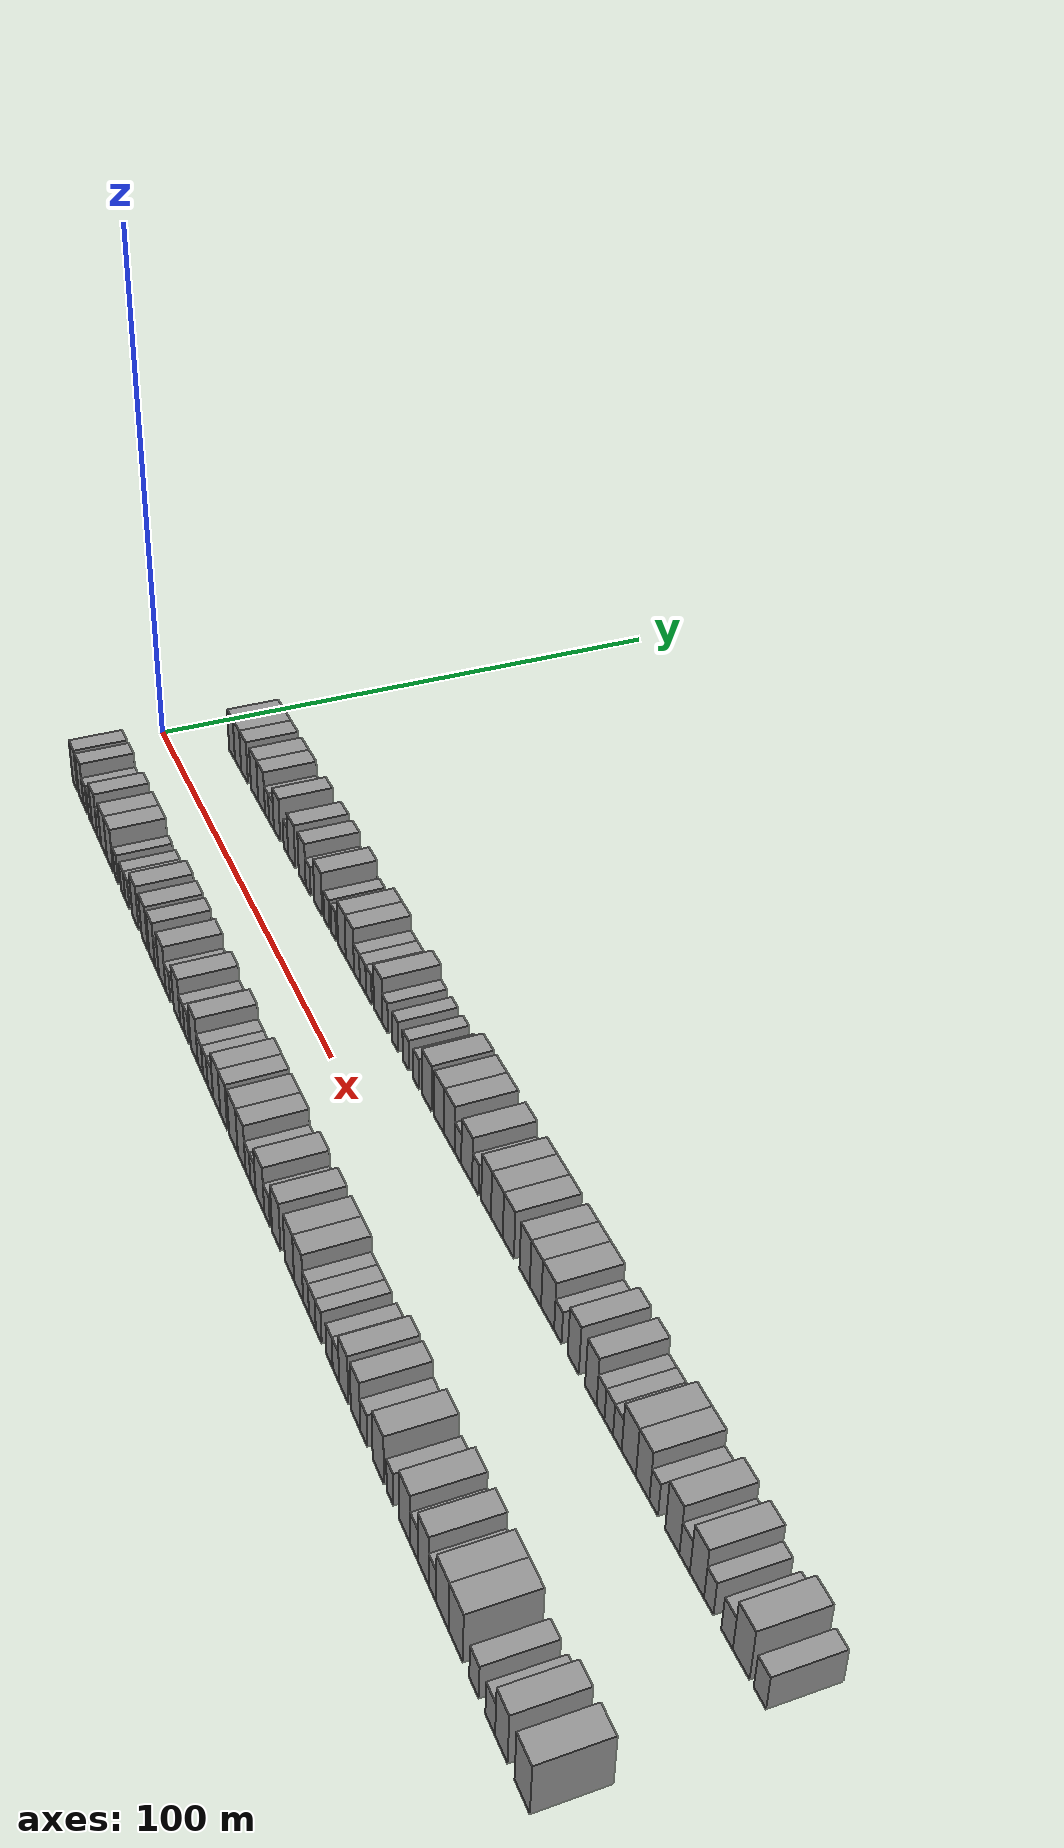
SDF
<sdf version="1.6">
 <world name="default">
  <scene>
   <sky><clouds><speed>12</speed></clouds></sky>
   <ambient>0.4 0.4 0.4 1</ambient>
   <background>0.7 0.7 0.7 1</background>
   <shadows>1</shadows>
  </scene>
  <gravity>0 0 -9.8066</gravity>
  <magnetic_field>6e-06 2.3e-05 -4.2e-05</magnetic_field>
  <physics default="0" name="default_physics" type="ode">
   <ode>
    <solver>
     <type>quick</type>
     <iters>10</iters>
     <sor>1.0</sor>
     <use_dynamic_moi_rescaling>0</use_dynamic_moi_rescaling>
    </solver>
    <constraints>
     <cfm>0</cfm>
     <erp>0.2</erp>
     <contact_max_correcting_vel>100</contact_max_correcting_vel>
     <contact_surface_layer>0.001</contact_surface_layer>
    </constraints>
   </ode>
   <max_step_size>0.004</max_step_size>
   <real_time_factor>1</real_time_factor>
   <real_time_update_rate>250</real_time_update_rate>
  </physics>
  <light name="sun" type="directional">
   <pose>0 0 10 0 0 0</pose>
   <diffuse>0.8 0.8 0.8 1</diffuse>
   <specular>0.2 0.2 0.2 1</specular>
   <attenuation>
    <range>1000</range>
    <constant>0.9</constant>
    <linear>0.01</linear>
    <quadratic>0.001</quadratic>
   </attenuation>
   <direction>-0.5 0.1 -0.9</direction>
  </light>
  <model name="building_1">
   <static>1</static>
   <pose>11.8743 15.0000 0 0.000000 0.000000 1.570796</pose>
   <link name="link">
    <pose>0 0 4.50 0 0 0</pose>
    <collision name="collision"><geometry><box><size>10.0000 3.7485 9.0000</size></box></geometry></collision>
    <visual name="visual">
     <cast_shadows>0</cast_shadows>
     <geometry><box><size>10.0000 3.7485 9.0000</size></box></geometry>
     <material>
      <script>
       <uri>model://grey_wall/materials/scripts</uri>
       <uri>model://grey_wall/materials/textures</uri>
       <name>vrc/grey_wall</name>
      </script>
     </material>
    </visual>
   </link>
  </model>
  <model name="building_2">
   <static>1</static>
   <pose>15.7916 15.0000 0 0.000000 0.000000 1.570796</pose>
   <link name="link">
    <pose>0 0 4.50 0 0 0</pose>
    <collision name="collision"><geometry><box><size>10.0000 4.0861 9.0000</size></box></geometry></collision>
    <visual name="visual">
     <cast_shadows>0</cast_shadows>
     <geometry><box><size>10.0000 4.0861 9.0000</size></box></geometry>
     <material>
      <script>
       <uri>model://grey_wall/materials/scripts</uri>
       <uri>model://grey_wall/materials/textures</uri>
       <name>vrc/grey_wall</name>
      </script>
     </material>
    </visual>
   </link>
  </model>
  <model name="building_3">
   <static>1</static>
   <pose>19.9500 15.0000 0 0.000000 0.000000 1.570796</pose>
   <link name="link">
    <pose>0 0 4.50 0 0 0</pose>
    <collision name="collision"><geometry><box><size>10.0000 4.2307 9.0000</size></box></geometry></collision>
    <visual name="visual">
     <cast_shadows>0</cast_shadows>
     <geometry><box><size>10.0000 4.2307 9.0000</size></box></geometry>
     <material>
      <script>
       <uri>model://grey_wall/materials/scripts</uri>
       <uri>model://grey_wall/materials/textures</uri>
       <name>vrc/grey_wall</name>
      </script>
     </material>
    </visual>
   </link>
  </model>
  <model name="building_4">
   <static>1</static>
   <pose>26.2549 15.0000 0 0.000000 0.000000 1.570796</pose>
   <link name="link">
    <pose>0 0 4.50 0 0 0</pose>
    <collision name="collision"><geometry><box><size>10.0000 4.3791 9.0000</size></box></geometry></collision>
    <visual name="visual">
     <cast_shadows>0</cast_shadows>
     <geometry><box><size>10.0000 4.3791 9.0000</size></box></geometry>
     <material>
      <script>
       <uri>model://grey_wall/materials/scripts</uri>
       <uri>model://grey_wall/materials/textures</uri>
       <name>vrc/grey_wall</name>
      </script>
     </material>
    </visual>
   </link>
  </model>
  <model name="building_5">
   <static>1</static>
   <pose>30.5329 15.0000 0 0.000000 0.000000 1.570796</pose>
   <link name="link">
    <pose>0 0 4.50 0 0 0</pose>
    <collision name="collision"><geometry><box><size>10.0000 4.1769 9.0000</size></box></geometry></collision>
    <visual name="visual">
     <cast_shadows>0</cast_shadows>
     <geometry><box><size>10.0000 4.1769 9.0000</size></box></geometry>
     <material>
      <script>
       <uri>model://grey_wall/materials/scripts</uri>
       <uri>model://grey_wall/materials/textures</uri>
       <name>vrc/grey_wall</name>
      </script>
     </material>
    </visual>
   </link>
  </model>
  <model name="building_6">
   <static>1</static>
   <pose>33.8588 15.0000 0 0.000000 0.000000 1.570796</pose>
   <link name="link">
    <pose>0 0 3.00 0 0 0</pose>
    <collision name="collision"><geometry><box><size>10.0000 2.4749 6.0000</size></box></geometry></collision>
    <visual name="visual">
     <cast_shadows>0</cast_shadows>
     <geometry><box><size>10.0000 2.4749 6.0000</size></box></geometry>
     <material>
      <script>
       <uri>model://grey_wall/materials/scripts</uri>
       <uri>model://grey_wall/materials/textures</uri>
       <name>vrc/grey_wall</name>
      </script>
     </material>
    </visual>
   </link>
  </model>
  <model name="building_7">
   <static>1</static>
   <pose>36.5099 15.0000 0 0.000000 0.000000 1.570796</pose>
   <link name="link">
    <pose>0 0 3.00 0 0 0</pose>
    <collision name="collision"><geometry><box><size>10.0000 2.8275 6.0000</size></box></geometry></collision>
    <visual name="visual">
     <cast_shadows>0</cast_shadows>
     <geometry><box><size>10.0000 2.8275 6.0000</size></box></geometry>
     <material>
      <script>
       <uri>model://grey_wall/materials/scripts</uri>
       <uri>model://grey_wall/materials/textures</uri>
       <name>vrc/grey_wall</name>
      </script>
     </material>
    </visual>
   </link>
  </model>
  <model name="building_8">
   <static>1</static>
   <pose>39.7782 15.0000 0 0.000000 0.000000 1.570796</pose>
   <link name="link">
    <pose>0 0 4.50 0 0 0</pose>
    <collision name="collision"><geometry><box><size>10.0000 3.7091 9.0000</size></box></geometry></collision>
    <visual name="visual">
     <cast_shadows>0</cast_shadows>
     <geometry><box><size>10.0000 3.7091 9.0000</size></box></geometry>
     <material>
      <script>
       <uri>model://grey_wall/materials/scripts</uri>
       <uri>model://grey_wall/materials/textures</uri>
       <name>vrc/grey_wall</name>
      </script>
     </material>
    </visual>
   </link>
  </model>
  <model name="building_9">
   <static>1</static>
   <pose>44.9292 15.0000 0 0.000000 0.000000 1.570796</pose>
   <link name="link">
    <pose>0 0 3.00 0 0 0</pose>
    <collision name="collision"><geometry><box><size>10.0000 2.5927 6.0000</size></box></geometry></collision>
    <visual name="visual">
     <cast_shadows>0</cast_shadows>
     <geometry><box><size>10.0000 2.5927 6.0000</size></box></geometry>
     <material>
      <script>
       <uri>model://grey_wall/materials/scripts</uri>
       <uri>model://grey_wall/materials/textures</uri>
       <name>vrc/grey_wall</name>
      </script>
     </material>
    </visual>
   </link>
  </model>
  <model name="building_10">
   <static>1</static>
   <pose>48.2375 15.0000 0 0.000000 0.000000 1.570796</pose>
   <link name="link">
    <pose>0 0 4.50 0 0 0</pose>
    <collision name="collision"><geometry><box><size>10.0000 4.0239 9.0000</size></box></geometry></collision>
    <visual name="visual">
     <cast_shadows>0</cast_shadows>
     <geometry><box><size>10.0000 4.0239 9.0000</size></box></geometry>
     <material>
      <script>
       <uri>model://grey_wall/materials/scripts</uri>
       <uri>model://grey_wall/materials/textures</uri>
       <name>vrc/grey_wall</name>
      </script>
     </material>
    </visual>
   </link>
  </model>
  <model name="building_11">
   <static>1</static>
   <pose>54.1597 15.0000 0 0.000000 0.000000 1.570796</pose>
   <link name="link">
    <pose>0 0 4.50 0 0 0</pose>
    <collision name="collision"><geometry><box><size>10.0000 3.8205 9.0000</size></box></geometry></collision>
    <visual name="visual">
     <cast_shadows>0</cast_shadows>
     <geometry><box><size>10.0000 3.8205 9.0000</size></box></geometry>
     <material>
      <script>
       <uri>model://grey_wall/materials/scripts</uri>
       <uri>model://grey_wall/materials/textures</uri>
       <name>vrc/grey_wall</name>
      </script>
     </material>
    </visual>
   </link>
  </model>
  <model name="building_12">
   <static>1</static>
   <pose>57.4333 15.0000 0 0.000000 0.000000 1.570796</pose>
   <link name="link">
    <pose>0 0 3.00 0 0 0</pose>
    <collision name="collision"><geometry><box><size>10.0000 2.7268 6.0000</size></box></geometry></collision>
    <visual name="visual">
     <cast_shadows>0</cast_shadows>
     <geometry><box><size>10.0000 2.7268 6.0000</size></box></geometry>
     <material>
      <script>
       <uri>model://grey_wall/materials/scripts</uri>
       <uri>model://grey_wall/materials/textures</uri>
       <name>vrc/grey_wall</name>
      </script>
     </material>
    </visual>
   </link>
  </model>
  <model name="building_13">
   <static>1</static>
   <pose>62.8809 15.0000 0 0.000000 0.000000 1.570796</pose>
   <link name="link">
    <pose>0 0 4.50 0 0 0</pose>
    <collision name="collision"><geometry><box><size>10.0000 4.1684 9.0000</size></box></geometry></collision>
    <visual name="visual">
     <cast_shadows>0</cast_shadows>
     <geometry><box><size>10.0000 4.1684 9.0000</size></box></geometry>
     <material>
      <script>
       <uri>model://grey_wall/materials/scripts</uri>
       <uri>model://grey_wall/materials/textures</uri>
       <name>vrc/grey_wall</name>
      </script>
     </material>
    </visual>
   </link>
  </model>
  <model name="building_14">
   <static>1</static>
   <pose>67.3798 15.0000 0 0.000000 0.000000 1.570796</pose>
   <link name="link">
    <pose>0 0 3.00 0 0 0</pose>
    <collision name="collision"><geometry><box><size>10.0000 2.8293 6.0000</size></box></geometry></collision>
    <visual name="visual">
     <cast_shadows>0</cast_shadows>
     <geometry><box><size>10.0000 2.8293 6.0000</size></box></geometry>
     <material>
      <script>
       <uri>model://grey_wall/materials/scripts</uri>
       <uri>model://grey_wall/materials/textures</uri>
       <name>vrc/grey_wall</name>
      </script>
     </material>
    </visual>
   </link>
  </model>
  <model name="building_15">
   <static>1</static>
   <pose>70.9947 15.0000 0 0.000000 0.000000 1.570796</pose>
   <link name="link">
    <pose>0 0 3.00 0 0 0</pose>
    <collision name="collision"><geometry><box><size>10.0000 2.4004 6.0000</size></box></geometry></collision>
    <visual name="visual">
     <cast_shadows>0</cast_shadows>
     <geometry><box><size>10.0000 2.4004 6.0000</size></box></geometry>
     <material>
      <script>
       <uri>model://grey_wall/materials/scripts</uri>
       <uri>model://grey_wall/materials/textures</uri>
       <name>vrc/grey_wall</name>
      </script>
     </material>
    </visual>
   </link>
  </model>
  <model name="building_16">
   <static>1</static>
   <pose>75.1674 15.0000 0 0.000000 0.000000 1.570796</pose>
   <link name="link">
    <pose>0 0 4.50 0 0 0</pose>
    <collision name="collision"><geometry><box><size>10.0000 3.9452 9.0000</size></box></geometry></collision>
    <visual name="visual">
     <cast_shadows>0</cast_shadows>
     <geometry><box><size>10.0000 3.9452 9.0000</size></box></geometry>
     <material>
      <script>
       <uri>model://grey_wall/materials/scripts</uri>
       <uri>model://grey_wall/materials/textures</uri>
       <name>vrc/grey_wall</name>
      </script>
     </material>
    </visual>
   </link>
  </model>
  <model name="building_17">
   <static>1</static>
   <pose>79.1817 15.0000 0 0.000000 0.000000 1.570796</pose>
   <link name="link">
    <pose>0 0 4.50 0 0 0</pose>
    <collision name="collision"><geometry><box><size>10.0000 4.0834 9.0000</size></box></geometry></collision>
    <visual name="visual">
     <cast_shadows>0</cast_shadows>
     <geometry><box><size>10.0000 4.0834 9.0000</size></box></geometry>
     <material>
      <script>
       <uri>model://grey_wall/materials/scripts</uri>
       <uri>model://grey_wall/materials/textures</uri>
       <name>vrc/grey_wall</name>
      </script>
     </material>
    </visual>
   </link>
  </model>
  <model name="building_18">
   <static>1</static>
   <pose>82.6705 15.0000 0 0.000000 0.000000 1.570796</pose>
   <link name="link">
    <pose>0 0 3.00 0 0 0</pose>
    <collision name="collision"><geometry><box><size>10.0000 2.8942 6.0000</size></box></geometry></collision>
    <visual name="visual">
     <cast_shadows>0</cast_shadows>
     <geometry><box><size>10.0000 2.8942 6.0000</size></box></geometry>
     <material>
      <script>
       <uri>model://grey_wall/materials/scripts</uri>
       <uri>model://grey_wall/materials/textures</uri>
       <name>vrc/grey_wall</name>
      </script>
     </material>
    </visual>
   </link>
  </model>
  <model name="building_19">
   <static>1</static>
   <pose>85.6084 15.0000 0 0.000000 0.000000 1.570796</pose>
   <link name="link">
    <pose>0 0 3.00 0 0 0</pose>
    <collision name="collision"><geometry><box><size>10.0000 2.9817 6.0000</size></box></geometry></collision>
    <visual name="visual">
     <cast_shadows>0</cast_shadows>
     <geometry><box><size>10.0000 2.9817 6.0000</size></box></geometry>
     <material>
      <script>
       <uri>model://grey_wall/materials/scripts</uri>
       <uri>model://grey_wall/materials/textures</uri>
       <name>vrc/grey_wall</name>
      </script>
     </material>
    </visual>
   </link>
  </model>
  <model name="building_20">
   <static>1</static>
   <pose>88.4929 15.0000 0 0.000000 0.000000 1.570796</pose>
   <link name="link">
    <pose>0 0 3.00 0 0 0</pose>
    <collision name="collision"><geometry><box><size>10.0000 2.7872 6.0000</size></box></geometry></collision>
    <visual name="visual">
     <cast_shadows>0</cast_shadows>
     <geometry><box><size>10.0000 2.7872 6.0000</size></box></geometry>
     <material>
      <script>
       <uri>model://grey_wall/materials/scripts</uri>
       <uri>model://grey_wall/materials/textures</uri>
       <name>vrc/grey_wall</name>
      </script>
     </material>
    </visual>
   </link>
  </model>
  <model name="building_21">
   <static>1</static>
   <pose>92.8238 15.0000 0 0.000000 0.000000 1.570796</pose>
   <link name="link">
    <pose>0 0 4.50 0 0 0</pose>
    <collision name="collision"><geometry><box><size>10.0000 3.8746 9.0000</size></box></geometry></collision>
    <visual name="visual">
     <cast_shadows>0</cast_shadows>
     <geometry><box><size>10.0000 3.8746 9.0000</size></box></geometry>
     <material>
      <script>
       <uri>model://grey_wall/materials/scripts</uri>
       <uri>model://grey_wall/materials/textures</uri>
       <name>vrc/grey_wall</name>
      </script>
     </material>
    </visual>
   </link>
  </model>
  <model name="building_22">
   <static>1</static>
   <pose>96.0821 15.0000 0 0.000000 0.000000 1.570796</pose>
   <link name="link">
    <pose>0 0 3.00 0 0 0</pose>
    <collision name="collision"><geometry><box><size>10.0000 2.6420 6.0000</size></box></geometry></collision>
    <visual name="visual">
     <cast_shadows>0</cast_shadows>
     <geometry><box><size>10.0000 2.6420 6.0000</size></box></geometry>
     <material>
      <script>
       <uri>model://grey_wall/materials/scripts</uri>
       <uri>model://grey_wall/materials/textures</uri>
       <name>vrc/grey_wall</name>
      </script>
     </material>
    </visual>
   </link>
  </model>
  <model name="building_23">
   <static>1</static>
   <pose>100.7850 15.0000 0 0.000000 0.000000 1.570796</pose>
   <link name="link">
    <pose>0 0 3.00 0 0 0</pose>
    <collision name="collision"><geometry><box><size>10.0000 2.7638 6.0000</size></box></geometry></collision>
    <visual name="visual">
     <cast_shadows>0</cast_shadows>
     <geometry><box><size>10.0000 2.7638 6.0000</size></box></geometry>
     <material>
      <script>
       <uri>model://grey_wall/materials/scripts</uri>
       <uri>model://grey_wall/materials/textures</uri>
       <name>vrc/grey_wall</name>
      </script>
     </material>
    </visual>
   </link>
  </model>
  <model name="building_24">
   <static>1</static>
   <pose>105.5017 15.0000 0 0.000000 0.000000 1.570796</pose>
   <link name="link">
    <pose>0 0 3.00 0 0 0</pose>
    <collision name="collision"><geometry><box><size>10.0000 2.6697 6.0000</size></box></geometry></collision>
    <visual name="visual">
     <cast_shadows>0</cast_shadows>
     <geometry><box><size>10.0000 2.6697 6.0000</size></box></geometry>
     <material>
      <script>
       <uri>model://grey_wall/materials/scripts</uri>
       <uri>model://grey_wall/materials/textures</uri>
       <name>vrc/grey_wall</name>
      </script>
     </material>
    </visual>
   </link>
  </model>
  <model name="building_25">
   <static>1</static>
   <pose>110.1485 15.0000 0 0.000000 0.000000 1.570796</pose>
   <link name="link">
    <pose>0 0 3.00 0 0 0</pose>
    <collision name="collision"><geometry><box><size>10.0000 2.6238 6.0000</size></box></geometry></collision>
    <visual name="visual">
     <cast_shadows>0</cast_shadows>
     <geometry><box><size>10.0000 2.6238 6.0000</size></box></geometry>
     <material>
      <script>
       <uri>model://grey_wall/materials/scripts</uri>
       <uri>model://grey_wall/materials/textures</uri>
       <name>vrc/grey_wall</name>
      </script>
     </material>
    </visual>
   </link>
  </model>
  <model name="building_26">
   <static>1</static>
   <pose>114.5944 15.0000 0 0.000000 0.000000 1.570796</pose>
   <link name="link">
    <pose>0 0 4.50 0 0 0</pose>
    <collision name="collision"><geometry><box><size>10.0000 4.2680 9.0000</size></box></geometry></collision>
    <visual name="visual">
     <cast_shadows>0</cast_shadows>
     <geometry><box><size>10.0000 4.2680 9.0000</size></box></geometry>
     <material>
      <script>
       <uri>model://grey_wall/materials/scripts</uri>
       <uri>model://grey_wall/materials/textures</uri>
       <name>vrc/grey_wall</name>
      </script>
     </material>
    </visual>
   </link>
  </model>
  <model name="building_27">
   <static>1</static>
   <pose>119.8555 15.0000 0 0.000000 0.000000 1.570796</pose>
   <link name="link">
    <pose>0 0 4.50 0 0 0</pose>
    <collision name="collision"><geometry><box><size>10.0000 4.2542 9.0000</size></box></geometry></collision>
    <visual name="visual">
     <cast_shadows>0</cast_shadows>
     <geometry><box><size>10.0000 4.2542 9.0000</size></box></geometry>
     <material>
      <script>
       <uri>model://grey_wall/materials/scripts</uri>
       <uri>model://grey_wall/materials/textures</uri>
       <name>vrc/grey_wall</name>
      </script>
     </material>
    </visual>
   </link>
  </model>
  <model name="building_28">
   <static>1</static>
   <pose>124.1061 15.0000 0 0.000000 0.000000 1.570796</pose>
   <link name="link">
    <pose>0 0 4.50 0 0 0</pose>
    <collision name="collision"><geometry><box><size>10.0000 4.2471 9.0000</size></box></geometry></collision>
    <visual name="visual">
     <cast_shadows>0</cast_shadows>
     <geometry><box><size>10.0000 4.2471 9.0000</size></box></geometry>
     <material>
      <script>
       <uri>model://grey_wall/materials/scripts</uri>
       <uri>model://grey_wall/materials/textures</uri>
       <name>vrc/grey_wall</name>
      </script>
     </material>
    </visual>
   </link>
  </model>
  <model name="building_29">
   <static>1</static>
   <pose>127.5682 15.0000 0 0.000000 0.000000 1.570796</pose>
   <link name="link">
    <pose>0 0 3.00 0 0 0</pose>
    <collision name="collision"><geometry><box><size>10.0000 2.6771 6.0000</size></box></geometry></collision>
    <visual name="visual">
     <cast_shadows>0</cast_shadows>
     <geometry><box><size>10.0000 2.6771 6.0000</size></box></geometry>
     <material>
      <script>
       <uri>model://grey_wall/materials/scripts</uri>
       <uri>model://grey_wall/materials/textures</uri>
       <name>vrc/grey_wall</name>
      </script>
     </material>
    </visual>
   </link>
  </model>
  <model name="building_30">
   <static>1</static>
   <pose>131.0592 15.0000 0 0.000000 0.000000 1.570796</pose>
   <link name="link">
    <pose>0 0 4.50 0 0 0</pose>
    <collision name="collision"><geometry><box><size>10.0000 4.3049 9.0000</size></box></geometry></collision>
    <visual name="visual">
     <cast_shadows>0</cast_shadows>
     <geometry><box><size>10.0000 4.3049 9.0000</size></box></geometry>
     <material>
      <script>
       <uri>model://grey_wall/materials/scripts</uri>
       <uri>model://grey_wall/materials/textures</uri>
       <name>vrc/grey_wall</name>
      </script>
     </material>
    </visual>
   </link>
  </model>
  <model name="building_31">
   <static>1</static>
   <pose>134.4650 15.0000 0 0.000000 0.000000 1.570796</pose>
   <link name="link">
    <pose>0 0 3.00 0 0 0</pose>
    <collision name="collision"><geometry><box><size>10.0000 2.5067 6.0000</size></box></geometry></collision>
    <visual name="visual">
     <cast_shadows>0</cast_shadows>
     <geometry><box><size>10.0000 2.5067 6.0000</size></box></geometry>
     <material>
      <script>
       <uri>model://grey_wall/materials/scripts</uri>
       <uri>model://grey_wall/materials/textures</uri>
       <name>vrc/grey_wall</name>
      </script>
     </material>
    </visual>
   </link>
  </model>
  <model name="building_32">
   <static>1</static>
   <pose>138.5697 15.0000 0 0.000000 0.000000 1.570796</pose>
   <link name="link">
    <pose>0 0 4.50 0 0 0</pose>
    <collision name="collision"><geometry><box><size>10.0000 3.7027 9.0000</size></box></geometry></collision>
    <visual name="visual">
     <cast_shadows>0</cast_shadows>
     <geometry><box><size>10.0000 3.7027 9.0000</size></box></geometry>
     <material>
      <script>
       <uri>model://grey_wall/materials/scripts</uri>
       <uri>model://grey_wall/materials/textures</uri>
       <name>vrc/grey_wall</name>
      </script>
     </material>
    </visual>
   </link>
  </model>
  <model name="building_33">
   <static>1</static>
   <pose>142.6201 15.0000 0 0.000000 0.000000 1.570796</pose>
   <link name="link">
    <pose>0 0 4.50 0 0 0</pose>
    <collision name="collision"><geometry><box><size>10.0000 4.3982 9.0000</size></box></geometry></collision>
    <visual name="visual">
     <cast_shadows>0</cast_shadows>
     <geometry><box><size>10.0000 4.3982 9.0000</size></box></geometry>
     <material>
      <script>
       <uri>model://grey_wall/materials/scripts</uri>
       <uri>model://grey_wall/materials/textures</uri>
       <name>vrc/grey_wall</name>
      </script>
     </material>
    </visual>
   </link>
  </model>
  <model name="building_34">
   <static>1</static>
   <pose>146.8642 15.0000 0 0.000000 0.000000 1.570796</pose>
   <link name="link">
    <pose>0 0 4.50 0 0 0</pose>
    <collision name="collision"><geometry><box><size>10.0000 4.0901 9.0000</size></box></geometry></collision>
    <visual name="visual">
     <cast_shadows>0</cast_shadows>
     <geometry><box><size>10.0000 4.0901 9.0000</size></box></geometry>
     <material>
      <script>
       <uri>model://grey_wall/materials/scripts</uri>
       <uri>model://grey_wall/materials/textures</uri>
       <name>vrc/grey_wall</name>
      </script>
     </material>
    </visual>
   </link>
  </model>
  <model name="building_35">
   <static>1</static>
   <pose>152.7222 15.0000 0 0.000000 0.000000 1.570796</pose>
   <link name="link">
    <pose>0 0 4.50 0 0 0</pose>
    <collision name="collision"><geometry><box><size>10.0000 3.6258 9.0000</size></box></geometry></collision>
    <visual name="visual">
     <cast_shadows>0</cast_shadows>
     <geometry><box><size>10.0000 3.6258 9.0000</size></box></geometry>
     <material>
      <script>
       <uri>model://grey_wall/materials/scripts</uri>
       <uri>model://grey_wall/materials/textures</uri>
       <name>vrc/grey_wall</name>
      </script>
     </material>
    </visual>
   </link>
  </model>
  <model name="building_36">
   <static>1</static>
   <pose>156.4994 15.0000 0 0.000000 0.000000 1.570796</pose>
   <link name="link">
    <pose>0 0 4.50 0 0 0</pose>
    <collision name="collision"><geometry><box><size>10.0000 3.9287 9.0000</size></box></geometry></collision>
    <visual name="visual">
     <cast_shadows>0</cast_shadows>
     <geometry><box><size>10.0000 3.9287 9.0000</size></box></geometry>
     <material>
      <script>
       <uri>model://grey_wall/materials/scripts</uri>
       <uri>model://grey_wall/materials/textures</uri>
       <name>vrc/grey_wall</name>
      </script>
     </material>
    </visual>
   </link>
  </model>
  <model name="building_37">
   <static>1</static>
   <pose>160.6866 15.0000 0 0.000000 0.000000 1.570796</pose>
   <link name="link">
    <pose>0 0 4.50 0 0 0</pose>
    <collision name="collision"><geometry><box><size>10.0000 4.4457 9.0000</size></box></geometry></collision>
    <visual name="visual">
     <cast_shadows>0</cast_shadows>
     <geometry><box><size>10.0000 4.4457 9.0000</size></box></geometry>
     <material>
      <script>
       <uri>model://grey_wall/materials/scripts</uri>
       <uri>model://grey_wall/materials/textures</uri>
       <name>vrc/grey_wall</name>
      </script>
     </material>
    </visual>
   </link>
  </model>
  <model name="building_38">
   <static>1</static>
   <pose>164.1530 15.0000 0 0.000000 0.000000 1.570796</pose>
   <link name="link">
    <pose>0 0 3.00 0 0 0</pose>
    <collision name="collision"><geometry><box><size>10.0000 2.4872 6.0000</size></box></geometry></collision>
    <visual name="visual">
     <cast_shadows>0</cast_shadows>
     <geometry><box><size>10.0000 2.4872 6.0000</size></box></geometry>
     <material>
      <script>
       <uri>model://grey_wall/materials/scripts</uri>
       <uri>model://grey_wall/materials/textures</uri>
       <name>vrc/grey_wall</name>
      </script>
     </material>
    </visual>
   </link>
  </model>
  <model name="building_39">
   <static>1</static>
   <pose>169.2162 15.0000 0 0.000000 0.000000 1.570796</pose>
   <link name="link">
    <pose>0 0 4.50 0 0 0</pose>
    <collision name="collision"><geometry><box><size>10.0000 3.6392 9.0000</size></box></geometry></collision>
    <visual name="visual">
     <cast_shadows>0</cast_shadows>
     <geometry><box><size>10.0000 3.6392 9.0000</size></box></geometry>
     <material>
      <script>
       <uri>model://grey_wall/materials/scripts</uri>
       <uri>model://grey_wall/materials/textures</uri>
       <name>vrc/grey_wall</name>
      </script>
     </material>
    </visual>
   </link>
  </model>
  <model name="building_40">
   <static>1</static>
   <pose>174.8434 15.0000 0 0.000000 0.000000 1.570796</pose>
   <link name="link">
    <pose>0 0 4.50 0 0 0</pose>
    <collision name="collision"><geometry><box><size>10.0000 3.6151 9.0000</size></box></geometry></collision>
    <visual name="visual">
     <cast_shadows>0</cast_shadows>
     <geometry><box><size>10.0000 3.6151 9.0000</size></box></geometry>
     <material>
      <script>
       <uri>model://grey_wall/materials/scripts</uri>
       <uri>model://grey_wall/materials/textures</uri>
       <name>vrc/grey_wall</name>
      </script>
     </material>
    </visual>
   </link>
  </model>
  <model name="building_41">
   <static>1</static>
   <pose>177.8762 15.0000 0 0.000000 0.000000 1.570796</pose>
   <link name="link">
    <pose>0 0 3.00 0 0 0</pose>
    <collision name="collision"><geometry><box><size>10.0000 2.4505 6.0000</size></box></geometry></collision>
    <visual name="visual">
     <cast_shadows>0</cast_shadows>
     <geometry><box><size>10.0000 2.4505 6.0000</size></box></geometry>
     <material>
      <script>
       <uri>model://grey_wall/materials/scripts</uri>
       <uri>model://grey_wall/materials/textures</uri>
       <name>vrc/grey_wall</name>
      </script>
     </material>
    </visual>
   </link>
  </model>
  <model name="building_42">
   <static>1</static>
   <pose>180.4161 15.0000 0 0.000000 0.000000 1.570796</pose>
   <link name="link">
    <pose>0 0 3.00 0 0 0</pose>
    <collision name="collision"><geometry><box><size>10.0000 2.6292 6.0000</size></box></geometry></collision>
    <visual name="visual">
     <cast_shadows>0</cast_shadows>
     <geometry><box><size>10.0000 2.6292 6.0000</size></box></geometry>
     <material>
      <script>
       <uri>model://grey_wall/materials/scripts</uri>
       <uri>model://grey_wall/materials/textures</uri>
       <name>vrc/grey_wall</name>
      </script>
     </material>
    </visual>
   </link>
  </model>
  <model name="building_43">
   <static>1</static>
   <pose>183.0317 15.0000 0 0.000000 0.000000 1.570796</pose>
   <link name="link">
    <pose>0 0 3.00 0 0 0</pose>
    <collision name="collision"><geometry><box><size>10.0000 2.6020 6.0000</size></box></geometry></collision>
    <visual name="visual">
     <cast_shadows>0</cast_shadows>
     <geometry><box><size>10.0000 2.6020 6.0000</size></box></geometry>
     <material>
      <script>
       <uri>model://grey_wall/materials/scripts</uri>
       <uri>model://grey_wall/materials/textures</uri>
       <name>vrc/grey_wall</name>
      </script>
     </material>
    </visual>
   </link>
  </model>
  <model name="building_44">
   <static>1</static>
   <pose>186.4371 15.0000 0 0.000000 0.000000 1.570796</pose>
   <link name="link">
    <pose>0 0 4.50 0 0 0</pose>
    <collision name="collision"><geometry><box><size>10.0000 4.2088 9.0000</size></box></geometry></collision>
    <visual name="visual">
     <cast_shadows>0</cast_shadows>
     <geometry><box><size>10.0000 4.2088 9.0000</size></box></geometry>
     <material>
      <script>
       <uri>model://grey_wall/materials/scripts</uri>
       <uri>model://grey_wall/materials/textures</uri>
       <name>vrc/grey_wall</name>
      </script>
     </material>
    </visual>
   </link>
  </model>
  <model name="building_45">
   <static>1</static>
   <pose>190.4963 15.0000 0 0.000000 0.000000 1.570796</pose>
   <link name="link">
    <pose>0 0 4.50 0 0 0</pose>
    <collision name="collision"><geometry><box><size>10.0000 3.9095 9.0000</size></box></geometry></collision>
    <visual name="visual">
     <cast_shadows>0</cast_shadows>
     <geometry><box><size>10.0000 3.9095 9.0000</size></box></geometry>
     <material>
      <script>
       <uri>model://grey_wall/materials/scripts</uri>
       <uri>model://grey_wall/materials/textures</uri>
       <name>vrc/grey_wall</name>
      </script>
     </material>
    </visual>
   </link>
  </model>
  <model name="building_46">
   <static>1</static>
   <pose>193.6895 15.0000 0 0.000000 0.000000 1.570796</pose>
   <link name="link">
    <pose>0 0 3.00 0 0 0</pose>
    <collision name="collision"><geometry><box><size>10.0000 2.4771 6.0000</size></box></geometry></collision>
    <visual name="visual">
     <cast_shadows>0</cast_shadows>
     <geometry><box><size>10.0000 2.4771 6.0000</size></box></geometry>
     <material>
      <script>
       <uri>model://grey_wall/materials/scripts</uri>
       <uri>model://grey_wall/materials/textures</uri>
       <name>vrc/grey_wall</name>
      </script>
     </material>
    </visual>
   </link>
  </model>
  <model name="building_47">
   <static>1</static>
   <pose>198.8887 15.0000 0 0.000000 0.000000 1.570796</pose>
   <link name="link">
    <pose>0 0 4.50 0 0 0</pose>
    <collision name="collision"><geometry><box><size>10.0000 3.9212 9.0000</size></box></geometry></collision>
    <visual name="visual">
     <cast_shadows>0</cast_shadows>
     <geometry><box><size>10.0000 3.9212 9.0000</size></box></geometry>
     <material>
      <script>
       <uri>model://grey_wall/materials/scripts</uri>
       <uri>model://grey_wall/materials/textures</uri>
       <name>vrc/grey_wall</name>
      </script>
     </material>
    </visual>
   </link>
  </model>
  <model name="building_48">
   <static>1</static>
   <pose>202.2613 15.0000 0 0.000000 0.000000 1.570796</pose>
   <link name="link">
    <pose>0 0 3.00 0 0 0</pose>
    <collision name="collision"><geometry><box><size>10.0000 2.8240 6.0000</size></box></geometry></collision>
    <visual name="visual">
     <cast_shadows>0</cast_shadows>
     <geometry><box><size>10.0000 2.8240 6.0000</size></box></geometry>
     <material>
      <script>
       <uri>model://grey_wall/materials/scripts</uri>
       <uri>model://grey_wall/materials/textures</uri>
       <name>vrc/grey_wall</name>
      </script>
     </material>
    </visual>
   </link>
  </model>
  <model name="building_49">
   <static>1</static>
   <pose>205.5533 15.0000 0 0.000000 0.000000 1.570796</pose>
   <link name="link">
    <pose>0 0 4.50 0 0 0</pose>
    <collision name="collision"><geometry><box><size>10.0000 3.7601 9.0000</size></box></geometry></collision>
    <visual name="visual">
     <cast_shadows>0</cast_shadows>
     <geometry><box><size>10.0000 3.7601 9.0000</size></box></geometry>
     <material>
      <script>
       <uri>model://grey_wall/materials/scripts</uri>
       <uri>model://grey_wall/materials/textures</uri>
       <name>vrc/grey_wall</name>
      </script>
     </material>
    </visual>
   </link>
  </model>
  <model name="building_50">
   <static>1</static>
   <pose>208.6606 15.0000 0 0.000000 0.000000 1.570796</pose>
   <link name="link">
    <pose>0 0 3.00 0 0 0</pose>
    <collision name="collision"><geometry><box><size>10.0000 2.4545 6.0000</size></box></geometry></collision>
    <visual name="visual">
     <cast_shadows>0</cast_shadows>
     <geometry><box><size>10.0000 2.4545 6.0000</size></box></geometry>
     <material>
      <script>
       <uri>model://grey_wall/materials/scripts</uri>
       <uri>model://grey_wall/materials/textures</uri>
       <name>vrc/grey_wall</name>
      </script>
     </material>
    </visual>
   </link>
  </model>
  <model name="building_51">
   <static>1</static>
   <pose>213.3533 15.0000 0 0.000000 0.000000 1.570796</pose>
   <link name="link">
    <pose>0 0 3.00 0 0 0</pose>
    <collision name="collision"><geometry><box><size>10.0000 2.9310 6.0000</size></box></geometry></collision>
    <visual name="visual">
     <cast_shadows>0</cast_shadows>
     <geometry><box><size>10.0000 2.9310 6.0000</size></box></geometry>
     <material>
      <script>
       <uri>model://grey_wall/materials/scripts</uri>
       <uri>model://grey_wall/materials/textures</uri>
       <name>vrc/grey_wall</name>
      </script>
     </material>
    </visual>
   </link>
  </model>
  <model name="building_52">
   <static>1</static>
   <pose>216.9027 15.0000 0 0.000000 0.000000 1.570796</pose>
   <link name="link">
    <pose>0 0 4.50 0 0 0</pose>
    <collision name="collision"><geometry><box><size>10.0000 4.1677 9.0000</size></box></geometry></collision>
    <visual name="visual">
     <cast_shadows>0</cast_shadows>
     <geometry><box><size>10.0000 4.1677 9.0000</size></box></geometry>
     <material>
      <script>
       <uri>model://grey_wall/materials/scripts</uri>
       <uri>model://grey_wall/materials/textures</uri>
       <name>vrc/grey_wall</name>
      </script>
     </material>
    </visual>
   </link>
  </model>
  <model name="building_53">
   <static>1</static>
   <pose>221.4834 15.0000 0 0.000000 0.000000 1.570796</pose>
   <link name="link">
    <pose>0 0 3.00 0 0 0</pose>
    <collision name="collision"><geometry><box><size>10.0000 2.9938 6.0000</size></box></geometry></collision>
    <visual name="visual">
     <cast_shadows>0</cast_shadows>
     <geometry><box><size>10.0000 2.9938 6.0000</size></box></geometry>
     <material>
      <script>
       <uri>model://grey_wall/materials/scripts</uri>
       <uri>model://grey_wall/materials/textures</uri>
       <name>vrc/grey_wall</name>
      </script>
     </material>
    </visual>
   </link>
  </model>
  <model name="building_54">
   <static>1</static>
   <pose>11.8688 -15.0000 0 0.000000 0.000000 1.570796</pose>
   <link name="link">
    <pose>0 0 4.50 0 0 0</pose>
    <collision name="collision"><geometry><box><size>10.0000 3.7377 9.0000</size></box></geometry></collision>
    <visual name="visual">
     <cast_shadows>0</cast_shadows>
     <geometry><box><size>10.0000 3.7377 9.0000</size></box></geometry>
     <material>
      <script>
       <uri>model://grey_wall/materials/scripts</uri>
       <uri>model://grey_wall/materials/textures</uri>
       <name>vrc/grey_wall</name>
      </script>
     </material>
    </visual>
   </link>
  </model>
  <model name="building_55">
   <static>1</static>
   <pose>16.5794 -15.0000 0 0.000000 0.000000 1.570796</pose>
   <link name="link">
    <pose>0 0 4.50 0 0 0</pose>
    <collision name="collision"><geometry><box><size>10.0000 3.6836 9.0000</size></box></geometry></collision>
    <visual name="visual">
     <cast_shadows>0</cast_shadows>
     <geometry><box><size>10.0000 3.6836 9.0000</size></box></geometry>
     <material>
      <script>
       <uri>model://grey_wall/materials/scripts</uri>
       <uri>model://grey_wall/materials/textures</uri>
       <name>vrc/grey_wall</name>
      </script>
     </material>
    </visual>
   </link>
  </model>
  <model name="building_56">
   <static>1</static>
   <pose>19.8574 -15.0000 0 0.000000 0.000000 1.570796</pose>
   <link name="link">
    <pose>0 0 3.00 0 0 0</pose>
    <collision name="collision"><geometry><box><size>10.0000 2.8724 6.0000</size></box></geometry></collision>
    <visual name="visual">
     <cast_shadows>0</cast_shadows>
     <geometry><box><size>10.0000 2.8724 6.0000</size></box></geometry>
     <material>
      <script>
       <uri>model://grey_wall/materials/scripts</uri>
       <uri>model://grey_wall/materials/textures</uri>
       <name>vrc/grey_wall</name>
      </script>
     </material>
    </visual>
   </link>
  </model>
  <model name="building_57">
   <static>1</static>
   <pose>23.6391 -15.0000 0 0.000000 0.000000 1.570796</pose>
   <link name="link">
    <pose>0 0 3.00 0 0 0</pose>
    <collision name="collision"><geometry><box><size>10.0000 2.6911 6.0000</size></box></geometry></collision>
    <visual name="visual">
     <cast_shadows>0</cast_shadows>
     <geometry><box><size>10.0000 2.6911 6.0000</size></box></geometry>
     <material>
      <script>
       <uri>model://grey_wall/materials/scripts</uri>
       <uri>model://grey_wall/materials/textures</uri>
       <name>vrc/grey_wall</name>
      </script>
     </material>
    </visual>
   </link>
  </model>
  <model name="building_58">
   <static>1</static>
   <pose>26.8901 -15.0000 0 0.000000 0.000000 1.570796</pose>
   <link name="link">
    <pose>0 0 4.50 0 0 0</pose>
    <collision name="collision"><geometry><box><size>10.0000 3.8110 9.0000</size></box></geometry></collision>
    <visual name="visual">
     <cast_shadows>0</cast_shadows>
     <geometry><box><size>10.0000 3.8110 9.0000</size></box></geometry>
     <material>
      <script>
       <uri>model://grey_wall/materials/scripts</uri>
       <uri>model://grey_wall/materials/textures</uri>
       <name>vrc/grey_wall</name>
      </script>
     </material>
    </visual>
   </link>
  </model>
  <model name="building_59">
   <static>1</static>
   <pose>30.2438 -15.0000 0 0.000000 0.000000 1.570796</pose>
   <link name="link">
    <pose>0 0 3.00 0 0 0</pose>
    <collision name="collision"><geometry><box><size>10.0000 2.8964 6.0000</size></box></geometry></collision>
    <visual name="visual">
     <cast_shadows>0</cast_shadows>
     <geometry><box><size>10.0000 2.8964 6.0000</size></box></geometry>
     <material>
      <script>
       <uri>model://grey_wall/materials/scripts</uri>
       <uri>model://grey_wall/materials/textures</uri>
       <name>vrc/grey_wall</name>
      </script>
     </material>
    </visual>
   </link>
  </model>
  <model name="building_60">
   <static>1</static>
   <pose>33.8105 -15.0000 0 0.000000 0.000000 1.570796</pose>
   <link name="link">
    <pose>0 0 4.50 0 0 0</pose>
    <collision name="collision"><geometry><box><size>10.0000 4.2371 9.0000</size></box></geometry></collision>
    <visual name="visual">
     <cast_shadows>0</cast_shadows>
     <geometry><box><size>10.0000 4.2371 9.0000</size></box></geometry>
     <material>
      <script>
       <uri>model://grey_wall/materials/scripts</uri>
       <uri>model://grey_wall/materials/textures</uri>
       <name>vrc/grey_wall</name>
      </script>
     </material>
    </visual>
   </link>
  </model>
  <model name="building_61">
   <static>1</static>
   <pose>38.1423 -15.0000 0 0.000000 0.000000 1.570796</pose>
   <link name="link">
    <pose>0 0 4.50 0 0 0</pose>
    <collision name="collision"><geometry><box><size>10.0000 4.4265 9.0000</size></box></geometry></collision>
    <visual name="visual">
     <cast_shadows>0</cast_shadows>
     <geometry><box><size>10.0000 4.4265 9.0000</size></box></geometry>
     <material>
      <script>
       <uri>model://grey_wall/materials/scripts</uri>
       <uri>model://grey_wall/materials/textures</uri>
       <name>vrc/grey_wall</name>
      </script>
     </material>
    </visual>
   </link>
  </model>
  <model name="building_62">
   <static>1</static>
   <pose>42.6361 -15.0000 0 0.000000 0.000000 1.570796</pose>
   <link name="link">
    <pose>0 0 3.00 0 0 0</pose>
    <collision name="collision"><geometry><box><size>10.0000 2.5611 6.0000</size></box></geometry></collision>
    <visual name="visual">
     <cast_shadows>0</cast_shadows>
     <geometry><box><size>10.0000 2.5611 6.0000</size></box></geometry>
     <material>
      <script>
       <uri>model://grey_wall/materials/scripts</uri>
       <uri>model://grey_wall/materials/textures</uri>
       <name>vrc/grey_wall</name>
      </script>
     </material>
    </visual>
   </link>
  </model>
  <model name="building_63">
   <static>1</static>
   <pose>47.3484 -15.0000 0 0.000000 0.000000 1.570796</pose>
   <link name="link">
    <pose>0 0 3.00 0 0 0</pose>
    <collision name="collision"><geometry><box><size>10.0000 2.8635 6.0000</size></box></geometry></collision>
    <visual name="visual">
     <cast_shadows>0</cast_shadows>
     <geometry><box><size>10.0000 2.8635 6.0000</size></box></geometry>
     <material>
      <script>
       <uri>model://grey_wall/materials/scripts</uri>
       <uri>model://grey_wall/materials/textures</uri>
       <name>vrc/grey_wall</name>
      </script>
     </material>
    </visual>
   </link>
  </model>
  <model name="building_64">
   <static>1</static>
   <pose>50.1985 -15.0000 0 0.000000 0.000000 1.570796</pose>
   <link name="link">
    <pose>0 0 3.00 0 0 0</pose>
    <collision name="collision"><geometry><box><size>10.0000 2.8366 6.0000</size></box></geometry></collision>
    <visual name="visual">
     <cast_shadows>0</cast_shadows>
     <geometry><box><size>10.0000 2.8366 6.0000</size></box></geometry>
     <material>
      <script>
       <uri>model://grey_wall/materials/scripts</uri>
       <uri>model://grey_wall/materials/textures</uri>
       <name>vrc/grey_wall</name>
      </script>
     </material>
    </visual>
   </link>
  </model>
  <model name="building_65">
   <static>1</static>
   <pose>55.6811 -15.0000 0 0.000000 0.000000 1.570796</pose>
   <link name="link">
    <pose>0 0 4.50 0 0 0</pose>
    <collision name="collision"><geometry><box><size>10.0000 4.1286 9.0000</size></box></geometry></collision>
    <visual name="visual">
     <cast_shadows>0</cast_shadows>
     <geometry><box><size>10.0000 4.1286 9.0000</size></box></geometry>
     <material>
      <script>
       <uri>model://grey_wall/materials/scripts</uri>
       <uri>model://grey_wall/materials/textures</uri>
       <name>vrc/grey_wall</name>
      </script>
     </material>
    </visual>
   </link>
  </model>
  <model name="building_66">
   <static>1</static>
   <pose>61.7320 -15.0000 0 0.000000 0.000000 1.570796</pose>
   <link name="link">
    <pose>0 0 4.50 0 0 0</pose>
    <collision name="collision"><geometry><box><size>10.0000 3.9733 9.0000</size></box></geometry></collision>
    <visual name="visual">
     <cast_shadows>0</cast_shadows>
     <geometry><box><size>10.0000 3.9733 9.0000</size></box></geometry>
     <material>
      <script>
       <uri>model://grey_wall/materials/scripts</uri>
       <uri>model://grey_wall/materials/textures</uri>
       <name>vrc/grey_wall</name>
      </script>
     </material>
    </visual>
   </link>
  </model>
  <model name="building_67">
   <static>1</static>
   <pose>66.5283 -15.0000 0 0.000000 0.000000 1.570796</pose>
   <link name="link">
    <pose>0 0 4.50 0 0 0</pose>
    <collision name="collision"><geometry><box><size>10.0000 3.6192 9.0000</size></box></geometry></collision>
    <visual name="visual">
     <cast_shadows>0</cast_shadows>
     <geometry><box><size>10.0000 3.6192 9.0000</size></box></geometry>
     <material>
      <script>
       <uri>model://grey_wall/materials/scripts</uri>
       <uri>model://grey_wall/materials/textures</uri>
       <name>vrc/grey_wall</name>
      </script>
     </material>
    </visual>
   </link>
  </model>
  <model name="building_68">
   <static>1</static>
   <pose>69.5654 -15.0000 0 0.000000 0.000000 1.570796</pose>
   <link name="link">
    <pose>0 0 3.00 0 0 0</pose>
    <collision name="collision"><geometry><box><size>10.0000 2.4549 6.0000</size></box></geometry></collision>
    <visual name="visual">
     <cast_shadows>0</cast_shadows>
     <geometry><box><size>10.0000 2.4549 6.0000</size></box></geometry>
     <material>
      <script>
       <uri>model://grey_wall/materials/scripts</uri>
       <uri>model://grey_wall/materials/textures</uri>
       <name>vrc/grey_wall</name>
      </script>
     </material>
    </visual>
   </link>
  </model>
  <model name="building_69">
   <static>1</static>
   <pose>72.8807 -15.0000 0 0.000000 0.000000 1.570796</pose>
   <link name="link">
    <pose>0 0 4.50 0 0 0</pose>
    <collision name="collision"><geometry><box><size>10.0000 4.1757 9.0000</size></box></geometry></collision>
    <visual name="visual">
     <cast_shadows>0</cast_shadows>
     <geometry><box><size>10.0000 4.1757 9.0000</size></box></geometry>
     <material>
      <script>
       <uri>model://grey_wall/materials/scripts</uri>
       <uri>model://grey_wall/materials/textures</uri>
       <name>vrc/grey_wall</name>
      </script>
     </material>
    </visual>
   </link>
  </model>
  <model name="building_70">
   <static>1</static>
   <pose>76.4175 -15.0000 0 0.000000 0.000000 1.570796</pose>
   <link name="link">
    <pose>0 0 3.00 0 0 0</pose>
    <collision name="collision"><geometry><box><size>10.0000 2.8979 6.0000</size></box></geometry></collision>
    <visual name="visual">
     <cast_shadows>0</cast_shadows>
     <geometry><box><size>10.0000 2.8979 6.0000</size></box></geometry>
     <material>
      <script>
       <uri>model://grey_wall/materials/scripts</uri>
       <uri>model://grey_wall/materials/textures</uri>
       <name>vrc/grey_wall</name>
      </script>
     </material>
    </visual>
   </link>
  </model>
  <model name="building_71">
   <static>1</static>
   <pose>81.8172 -15.0000 0 0.000000 0.000000 1.570796</pose>
   <link name="link">
    <pose>0 0 4.50 0 0 0</pose>
    <collision name="collision"><geometry><box><size>10.0000 3.9014 9.0000</size></box></geometry></collision>
    <visual name="visual">
     <cast_shadows>0</cast_shadows>
     <geometry><box><size>10.0000 3.9014 9.0000</size></box></geometry>
     <material>
      <script>
       <uri>model://grey_wall/materials/scripts</uri>
       <uri>model://grey_wall/materials/textures</uri>
       <name>vrc/grey_wall</name>
      </script>
     </material>
    </visual>
   </link>
  </model>
  <model name="building_72">
   <static>1</static>
   <pose>85.0114 -15.0000 0 0.000000 0.000000 1.570796</pose>
   <link name="link">
    <pose>0 0 3.00 0 0 0</pose>
    <collision name="collision"><geometry><box><size>10.0000 2.4870 6.0000</size></box></geometry></collision>
    <visual name="visual">
     <cast_shadows>0</cast_shadows>
     <geometry><box><size>10.0000 2.4870 6.0000</size></box></geometry>
     <material>
      <script>
       <uri>model://grey_wall/materials/scripts</uri>
       <uri>model://grey_wall/materials/textures</uri>
       <name>vrc/grey_wall</name>
      </script>
     </material>
    </visual>
   </link>
  </model>
  <model name="building_73">
   <static>1</static>
   <pose>87.5904 -15.0000 0 0.000000 0.000000 1.570796</pose>
   <link name="link">
    <pose>0 0 3.00 0 0 0</pose>
    <collision name="collision"><geometry><box><size>10.0000 2.6711 6.0000</size></box></geometry></collision>
    <visual name="visual">
     <cast_shadows>0</cast_shadows>
     <geometry><box><size>10.0000 2.6711 6.0000</size></box></geometry>
     <material>
      <script>
       <uri>model://grey_wall/materials/scripts</uri>
       <uri>model://grey_wall/materials/textures</uri>
       <name>vrc/grey_wall</name>
      </script>
     </material>
    </visual>
   </link>
  </model>
  <model name="building_74">
   <static>1</static>
   <pose>91.8857 -15.0000 0 0.000000 0.000000 1.570796</pose>
   <link name="link">
    <pose>0 0 4.50 0 0 0</pose>
    <collision name="collision"><geometry><box><size>10.0000 3.9196 9.0000</size></box></geometry></collision>
    <visual name="visual">
     <cast_shadows>0</cast_shadows>
     <geometry><box><size>10.0000 3.9196 9.0000</size></box></geometry>
     <material>
      <script>
       <uri>model://grey_wall/materials/scripts</uri>
       <uri>model://grey_wall/materials/textures</uri>
       <name>vrc/grey_wall</name>
      </script>
     </material>
    </visual>
   </link>
  </model>
  <model name="building_75">
   <static>1</static>
   <pose>95.2923 -15.0000 0 0.000000 0.000000 1.570796</pose>
   <link name="link">
    <pose>0 0 3.00 0 0 0</pose>
    <collision name="collision"><geometry><box><size>10.0000 2.8935 6.0000</size></box></geometry></collision>
    <visual name="visual">
     <cast_shadows>0</cast_shadows>
     <geometry><box><size>10.0000 2.8935 6.0000</size></box></geometry>
     <material>
      <script>
       <uri>model://grey_wall/materials/scripts</uri>
       <uri>model://grey_wall/materials/textures</uri>
       <name>vrc/grey_wall</name>
      </script>
     </material>
    </visual>
   </link>
  </model>
  <model name="building_76">
   <static>1</static>
   <pose>98.0653 -15.0000 0 0.000000 0.000000 1.570796</pose>
   <link name="link">
    <pose>0 0 3.00 0 0 0</pose>
    <collision name="collision"><geometry><box><size>10.0000 2.6526 6.0000</size></box></geometry></collision>
    <visual name="visual">
     <cast_shadows>0</cast_shadows>
     <geometry><box><size>10.0000 2.6526 6.0000</size></box></geometry>
     <material>
      <script>
       <uri>model://grey_wall/materials/scripts</uri>
       <uri>model://grey_wall/materials/textures</uri>
       <name>vrc/grey_wall</name>
      </script>
     </material>
    </visual>
   </link>
  </model>
  <model name="building_77">
   <static>1</static>
   <pose>100.8363 -15.0000 0 0.000000 0.000000 1.570796</pose>
   <link name="link">
    <pose>0 0 3.00 0 0 0</pose>
    <collision name="collision"><geometry><box><size>10.0000 2.8894 6.0000</size></box></geometry></collision>
    <visual name="visual">
     <cast_shadows>0</cast_shadows>
     <geometry><box><size>10.0000 2.8894 6.0000</size></box></geometry>
     <material>
      <script>
       <uri>model://grey_wall/materials/scripts</uri>
       <uri>model://grey_wall/materials/textures</uri>
       <name>vrc/grey_wall</name>
      </script>
     </material>
    </visual>
   </link>
  </model>
  <model name="building_78">
   <static>1</static>
   <pose>104.2514 -15.0000 0 0.000000 0.000000 1.570796</pose>
   <link name="link">
    <pose>0 0 4.50 0 0 0</pose>
    <collision name="collision"><geometry><box><size>10.0000 3.9408 9.0000</size></box></geometry></collision>
    <visual name="visual">
     <cast_shadows>0</cast_shadows>
     <geometry><box><size>10.0000 3.9408 9.0000</size></box></geometry>
     <material>
      <script>
       <uri>model://grey_wall/materials/scripts</uri>
       <uri>model://grey_wall/materials/textures</uri>
       <name>vrc/grey_wall</name>
      </script>
     </material>
    </visual>
   </link>
  </model>
  <model name="building_79">
   <static>1</static>
   <pose>108.0422 -15.0000 0 0.000000 0.000000 1.570796</pose>
   <link name="link">
    <pose>0 0 4.50 0 0 0</pose>
    <collision name="collision"><geometry><box><size>10.0000 3.6409 9.0000</size></box></geometry></collision>
    <visual name="visual">
     <cast_shadows>0</cast_shadows>
     <geometry><box><size>10.0000 3.6409 9.0000</size></box></geometry>
     <material>
      <script>
       <uri>model://grey_wall/materials/scripts</uri>
       <uri>model://grey_wall/materials/textures</uri>
       <name>vrc/grey_wall</name>
      </script>
     </material>
    </visual>
   </link>
  </model>
  <model name="building_80">
   <static>1</static>
   <pose>113.0856 -15.0000 0 0.000000 0.000000 1.570796</pose>
   <link name="link">
    <pose>0 0 4.50 0 0 0</pose>
    <collision name="collision"><geometry><box><size>10.0000 4.4459 9.0000</size></box></geometry></collision>
    <visual name="visual">
     <cast_shadows>0</cast_shadows>
     <geometry><box><size>10.0000 4.4459 9.0000</size></box></geometry>
     <material>
      <script>
       <uri>model://grey_wall/materials/scripts</uri>
       <uri>model://grey_wall/materials/textures</uri>
       <name>vrc/grey_wall</name>
      </script>
     </material>
    </visual>
   </link>
  </model>
  <model name="building_81">
   <static>1</static>
   <pose>117.2634 -15.0000 0 0.000000 0.000000 1.570796</pose>
   <link name="link">
    <pose>0 0 4.50 0 0 0</pose>
    <collision name="collision"><geometry><box><size>10.0000 3.9097 9.0000</size></box></geometry></collision>
    <visual name="visual">
     <cast_shadows>0</cast_shadows>
     <geometry><box><size>10.0000 3.9097 9.0000</size></box></geometry>
     <material>
      <script>
       <uri>model://grey_wall/materials/scripts</uri>
       <uri>model://grey_wall/materials/textures</uri>
       <name>vrc/grey_wall</name>
      </script>
     </material>
    </visual>
   </link>
  </model>
  <model name="building_82">
   <static>1</static>
   <pose>120.4411 -15.0000 0 0.000000 0.000000 1.570796</pose>
   <link name="link">
    <pose>0 0 3.00 0 0 0</pose>
    <collision name="collision"><geometry><box><size>10.0000 2.4455 6.0000</size></box></geometry></collision>
    <visual name="visual">
     <cast_shadows>0</cast_shadows>
     <geometry><box><size>10.0000 2.4455 6.0000</size></box></geometry>
     <material>
      <script>
       <uri>model://grey_wall/materials/scripts</uri>
       <uri>model://grey_wall/materials/textures</uri>
       <name>vrc/grey_wall</name>
      </script>
     </material>
    </visual>
   </link>
  </model>
  <model name="building_83">
   <static>1</static>
   <pose>122.9377 -15.0000 0 0.000000 0.000000 1.570796</pose>
   <link name="link">
    <pose>0 0 3.00 0 0 0</pose>
    <collision name="collision"><geometry><box><size>10.0000 2.5479 6.0000</size></box></geometry></collision>
    <visual name="visual">
     <cast_shadows>0</cast_shadows>
     <geometry><box><size>10.0000 2.5479 6.0000</size></box></geometry>
     <material>
      <script>
       <uri>model://grey_wall/materials/scripts</uri>
       <uri>model://grey_wall/materials/textures</uri>
       <name>vrc/grey_wall</name>
      </script>
     </material>
    </visual>
   </link>
  </model>
  <model name="building_84">
   <static>1</static>
   <pose>126.3077 -15.0000 0 0.000000 0.000000 1.570796</pose>
   <link name="link">
    <pose>0 0 4.50 0 0 0</pose>
    <collision name="collision"><geometry><box><size>10.0000 4.1920 9.0000</size></box></geometry></collision>
    <visual name="visual">
     <cast_shadows>0</cast_shadows>
     <geometry><box><size>10.0000 4.1920 9.0000</size></box></geometry>
     <material>
      <script>
       <uri>model://grey_wall/materials/scripts</uri>
       <uri>model://grey_wall/materials/textures</uri>
       <name>vrc/grey_wall</name>
      </script>
     </material>
    </visual>
   </link>
  </model>
  <model name="building_85">
   <static>1</static>
   <pose>129.7392 -15.0000 0 0.000000 0.000000 1.570796</pose>
   <link name="link">
    <pose>0 0 3.00 0 0 0</pose>
    <collision name="collision"><geometry><box><size>10.0000 2.6710 6.0000</size></box></geometry></collision>
    <visual name="visual">
     <cast_shadows>0</cast_shadows>
     <geometry><box><size>10.0000 2.6710 6.0000</size></box></geometry>
     <material>
      <script>
       <uri>model://grey_wall/materials/scripts</uri>
       <uri>model://grey_wall/materials/textures</uri>
       <name>vrc/grey_wall</name>
      </script>
     </material>
    </visual>
   </link>
  </model>
  <model name="building_86">
   <static>1</static>
   <pose>134.0358 -15.0000 0 0.000000 0.000000 1.570796</pose>
   <link name="link">
    <pose>0 0 4.50 0 0 0</pose>
    <collision name="collision"><geometry><box><size>10.0000 3.9222 9.0000</size></box></geometry></collision>
    <visual name="visual">
     <cast_shadows>0</cast_shadows>
     <geometry><box><size>10.0000 3.9222 9.0000</size></box></geometry>
     <material>
      <script>
       <uri>model://grey_wall/materials/scripts</uri>
       <uri>model://grey_wall/materials/textures</uri>
       <name>vrc/grey_wall</name>
      </script>
     </material>
    </visual>
   </link>
  </model>
  <model name="building_87">
   <static>1</static>
   <pose>140.0731 -15.0000 0 0.000000 0.000000 1.570796</pose>
   <link name="link">
    <pose>0 0 4.50 0 0 0</pose>
    <collision name="collision"><geometry><box><size>10.0000 4.1524 9.0000</size></box></geometry></collision>
    <visual name="visual">
     <cast_shadows>0</cast_shadows>
     <geometry><box><size>10.0000 4.1524 9.0000</size></box></geometry>
     <material>
      <script>
       <uri>model://grey_wall/materials/scripts</uri>
       <uri>model://grey_wall/materials/textures</uri>
       <name>vrc/grey_wall</name>
      </script>
     </material>
    </visual>
   </link>
  </model>
  <model name="building_88">
   <static>1</static>
   <pose>144.1564 -15.0000 0 0.000000 0.000000 1.570796</pose>
   <link name="link">
    <pose>0 0 4.50 0 0 0</pose>
    <collision name="collision"><geometry><box><size>10.0000 4.0142 9.0000</size></box></geometry></collision>
    <visual name="visual">
     <cast_shadows>0</cast_shadows>
     <geometry><box><size>10.0000 4.0142 9.0000</size></box></geometry>
     <material>
      <script>
       <uri>model://grey_wall/materials/scripts</uri>
       <uri>model://grey_wall/materials/textures</uri>
       <name>vrc/grey_wall</name>
      </script>
     </material>
    </visual>
   </link>
  </model>
  <model name="building_89">
   <static>1</static>
   <pose>147.4107 -15.0000 0 0.000000 0.000000 1.570796</pose>
   <link name="link">
    <pose>0 0 3.00 0 0 0</pose>
    <collision name="collision"><geometry><box><size>10.0000 2.4943 6.0000</size></box></geometry></collision>
    <visual name="visual">
     <cast_shadows>0</cast_shadows>
     <geometry><box><size>10.0000 2.4943 6.0000</size></box></geometry>
     <material>
      <script>
       <uri>model://grey_wall/materials/scripts</uri>
       <uri>model://grey_wall/materials/textures</uri>
       <name>vrc/grey_wall</name>
      </script>
     </material>
    </visual>
   </link>
  </model>
  <model name="building_90">
   <static>1</static>
   <pose>150.1211 -15.0000 0 0.000000 0.000000 1.570796</pose>
   <link name="link">
    <pose>0 0 3.00 0 0 0</pose>
    <collision name="collision"><geometry><box><size>10.0000 2.9267 6.0000</size></box></geometry></collision>
    <visual name="visual">
     <cast_shadows>0</cast_shadows>
     <geometry><box><size>10.0000 2.9267 6.0000</size></box></geometry>
     <material>
      <script>
       <uri>model://grey_wall/materials/scripts</uri>
       <uri>model://grey_wall/materials/textures</uri>
       <name>vrc/grey_wall</name>
      </script>
     </material>
    </visual>
   </link>
  </model>
  <model name="building_91">
   <static>1</static>
   <pose>152.8282 -15.0000 0 0.000000 0.000000 1.570796</pose>
   <link name="link">
    <pose>0 0 3.00 0 0 0</pose>
    <collision name="collision"><geometry><box><size>10.0000 2.4874 6.0000</size></box></geometry></collision>
    <visual name="visual">
     <cast_shadows>0</cast_shadows>
     <geometry><box><size>10.0000 2.4874 6.0000</size></box></geometry>
     <material>
      <script>
       <uri>model://grey_wall/materials/scripts</uri>
       <uri>model://grey_wall/materials/textures</uri>
       <name>vrc/grey_wall</name>
      </script>
     </material>
    </visual>
   </link>
  </model>
  <model name="building_92">
   <static>1</static>
   <pose>157.3483 -15.0000 0 0.000000 0.000000 1.570796</pose>
   <link name="link">
    <pose>0 0 3.00 0 0 0</pose>
    <collision name="collision"><geometry><box><size>10.0000 2.5528 6.0000</size></box></geometry></collision>
    <visual name="visual">
     <cast_shadows>0</cast_shadows>
     <geometry><box><size>10.0000 2.5528 6.0000</size></box></geometry>
     <material>
      <script>
       <uri>model://grey_wall/materials/scripts</uri>
       <uri>model://grey_wall/materials/textures</uri>
       <name>vrc/grey_wall</name>
      </script>
     </material>
    </visual>
   </link>
  </model>
  <model name="building_93">
   <static>1</static>
   <pose>159.9591 -15.0000 0 0.000000 0.000000 1.570796</pose>
   <link name="link">
    <pose>0 0 3.00 0 0 0</pose>
    <collision name="collision"><geometry><box><size>10.0000 2.6688 6.0000</size></box></geometry></collision>
    <visual name="visual">
     <cast_shadows>0</cast_shadows>
     <geometry><box><size>10.0000 2.6688 6.0000</size></box></geometry>
     <material>
      <script>
       <uri>model://grey_wall/materials/scripts</uri>
       <uri>model://grey_wall/materials/textures</uri>
       <name>vrc/grey_wall</name>
      </script>
     </material>
    </visual>
   </link>
  </model>
  <model name="building_94">
   <static>1</static>
   <pose>163.1216 -15.0000 0 0.000000 0.000000 1.570796</pose>
   <link name="link">
    <pose>0 0 4.50 0 0 0</pose>
    <collision name="collision"><geometry><box><size>10.0000 3.6561 9.0000</size></box></geometry></collision>
    <visual name="visual">
     <cast_shadows>0</cast_shadows>
     <geometry><box><size>10.0000 3.6561 9.0000</size></box></geometry>
     <material>
      <script>
       <uri>model://grey_wall/materials/scripts</uri>
       <uri>model://grey_wall/materials/textures</uri>
       <name>vrc/grey_wall</name>
      </script>
     </material>
    </visual>
   </link>
  </model>
  <model name="building_95">
   <static>1</static>
   <pose>167.7519 -15.0000 0 0.000000 0.000000 1.570796</pose>
   <link name="link">
    <pose>0 0 4.50 0 0 0</pose>
    <collision name="collision"><geometry><box><size>10.0000 3.6045 9.0000</size></box></geometry></collision>
    <visual name="visual">
     <cast_shadows>0</cast_shadows>
     <geometry><box><size>10.0000 3.6045 9.0000</size></box></geometry>
     <material>
      <script>
       <uri>model://grey_wall/materials/scripts</uri>
       <uri>model://grey_wall/materials/textures</uri>
       <name>vrc/grey_wall</name>
      </script>
     </material>
    </visual>
   </link>
  </model>
  <model name="building_96">
   <static>1</static>
   <pose>170.9366 -15.0000 0 0.000000 0.000000 1.570796</pose>
   <link name="link">
    <pose>0 0 3.00 0 0 0</pose>
    <collision name="collision"><geometry><box><size>10.0000 2.7650 6.0000</size></box></geometry></collision>
    <visual name="visual">
     <cast_shadows>0</cast_shadows>
     <geometry><box><size>10.0000 2.7650 6.0000</size></box></geometry>
     <material>
      <script>
       <uri>model://grey_wall/materials/scripts</uri>
       <uri>model://grey_wall/materials/textures</uri>
       <name>vrc/grey_wall</name>
      </script>
     </material>
    </visual>
   </link>
  </model>
  <model name="building_97">
   <static>1</static>
   <pose>176.4247 -15.0000 0 0.000000 0.000000 1.570796</pose>
   <link name="link">
    <pose>0 0 4.50 0 0 0</pose>
    <collision name="collision"><geometry><box><size>10.0000 4.2112 9.0000</size></box></geometry></collision>
    <visual name="visual">
     <cast_shadows>0</cast_shadows>
     <geometry><box><size>10.0000 4.2112 9.0000</size></box></geometry>
     <material>
      <script>
       <uri>model://grey_wall/materials/scripts</uri>
       <uri>model://grey_wall/materials/textures</uri>
       <name>vrc/grey_wall</name>
      </script>
     </material>
    </visual>
   </link>
  </model>
  <model name="building_98">
   <static>1</static>
   <pose>180.7450 -15.0000 0 0.000000 0.000000 1.570796</pose>
   <link name="link">
    <pose>0 0 3.00 0 0 0</pose>
    <collision name="collision"><geometry><box><size>10.0000 2.4293 6.0000</size></box></geometry></collision>
    <visual name="visual">
     <cast_shadows>0</cast_shadows>
     <geometry><box><size>10.0000 2.4293 6.0000</size></box></geometry>
     <material>
      <script>
       <uri>model://grey_wall/materials/scripts</uri>
       <uri>model://grey_wall/materials/textures</uri>
       <name>vrc/grey_wall</name>
      </script>
     </material>
    </visual>
   </link>
  </model>
  <model name="building_99">
   <static>1</static>
   <pose>185.9530 -15.0000 0 0.000000 0.000000 1.570796</pose>
   <link name="link">
    <pose>0 0 4.50 0 0 0</pose>
    <collision name="collision"><geometry><box><size>10.0000 3.9868 9.0000</size></box></geometry></collision>
    <visual name="visual">
     <cast_shadows>0</cast_shadows>
     <geometry><box><size>10.0000 3.9868 9.0000</size></box></geometry>
     <material>
      <script>
       <uri>model://grey_wall/materials/scripts</uri>
       <uri>model://grey_wall/materials/textures</uri>
       <name>vrc/grey_wall</name>
      </script>
     </material>
    </visual>
   </link>
  </model>
  <model name="building_100">
   <static>1</static>
   <pose>189.2060 -15.0000 0 0.000000 0.000000 1.570796</pose>
   <link name="link">
    <pose>0 0 3.00 0 0 0</pose>
    <collision name="collision"><geometry><box><size>10.0000 2.5192 6.0000</size></box></geometry></collision>
    <visual name="visual">
     <cast_shadows>0</cast_shadows>
     <geometry><box><size>10.0000 2.5192 6.0000</size></box></geometry>
     <material>
      <script>
       <uri>model://grey_wall/materials/scripts</uri>
       <uri>model://grey_wall/materials/textures</uri>
       <name>vrc/grey_wall</name>
      </script>
     </material>
    </visual>
   </link>
  </model>
  <model name="building_101">
   <static>1</static>
   <pose>192.3293 -15.0000 0 0.000000 0.000000 1.570796</pose>
   <link name="link">
    <pose>0 0 4.50 0 0 0</pose>
    <collision name="collision"><geometry><box><size>10.0000 3.7275 9.0000</size></box></geometry></collision>
    <visual name="visual">
     <cast_shadows>0</cast_shadows>
     <geometry><box><size>10.0000 3.7275 9.0000</size></box></geometry>
     <material>
      <script>
       <uri>model://grey_wall/materials/scripts</uri>
       <uri>model://grey_wall/materials/textures</uri>
       <name>vrc/grey_wall</name>
      </script>
     </material>
    </visual>
   </link>
  </model>
  <model name="building_102">
   <static>1</static>
   <pose>195.4604 -15.0000 0 0.000000 0.000000 1.570796</pose>
   <link name="link">
    <pose>0 0 3.00 0 0 0</pose>
    <collision name="collision"><geometry><box><size>10.0000 2.5348 6.0000</size></box></geometry></collision>
    <visual name="visual">
     <cast_shadows>0</cast_shadows>
     <geometry><box><size>10.0000 2.5348 6.0000</size></box></geometry>
     <material>
      <script>
       <uri>model://grey_wall/materials/scripts</uri>
       <uri>model://grey_wall/materials/textures</uri>
       <name>vrc/grey_wall</name>
      </script>
     </material>
    </visual>
   </link>
  </model>
  <model name="building_103">
   <static>1</static>
   <pose>198.7855 -15.0000 0 0.000000 0.000000 1.570796</pose>
   <link name="link">
    <pose>0 0 4.50 0 0 0</pose>
    <collision name="collision"><geometry><box><size>10.0000 4.1154 9.0000</size></box></geometry></collision>
    <visual name="visual">
     <cast_shadows>0</cast_shadows>
     <geometry><box><size>10.0000 4.1154 9.0000</size></box></geometry>
     <material>
      <script>
       <uri>model://grey_wall/materials/scripts</uri>
       <uri>model://grey_wall/materials/textures</uri>
       <name>vrc/grey_wall</name>
      </script>
     </material>
    </visual>
   </link>
  </model>
  <model name="building_104">
   <static>1</static>
   <pose>203.0848 -15.0000 0 0.000000 0.000000 1.570796</pose>
   <link name="link">
    <pose>0 0 4.50 0 0 0</pose>
    <collision name="collision"><geometry><box><size>10.0000 4.4832 9.0000</size></box></geometry></collision>
    <visual name="visual">
     <cast_shadows>0</cast_shadows>
     <geometry><box><size>10.0000 4.4832 9.0000</size></box></geometry>
     <material>
      <script>
       <uri>model://grey_wall/materials/scripts</uri>
       <uri>model://grey_wall/materials/textures</uri>
       <name>vrc/grey_wall</name>
      </script>
     </material>
    </visual>
   </link>
  </model>
  <model name="building_105">
   <static>1</static>
   <pose>208.7875 -15.0000 0 0.000000 0.000000 1.570796</pose>
   <link name="link">
    <pose>0 0 3.00 0 0 0</pose>
    <collision name="collision"><geometry><box><size>10.0000 2.9222 6.0000</size></box></geometry></collision>
    <visual name="visual">
     <cast_shadows>0</cast_shadows>
     <geometry><box><size>10.0000 2.9222 6.0000</size></box></geometry>
     <material>
      <script>
       <uri>model://grey_wall/materials/scripts</uri>
       <uri>model://grey_wall/materials/textures</uri>
       <name>vrc/grey_wall</name>
      </script>
     </material>
    </visual>
   </link>
  </model>
  <model name="building_106">
   <static>1</static>
   <pose>213.6928 -15.0000 0 0.000000 0.000000 1.570796</pose>
   <link name="link">
    <pose>0 0 3.00 0 0 0</pose>
    <collision name="collision"><geometry><box><size>10.0000 2.8884 6.0000</size></box></geometry></collision>
    <visual name="visual">
     <cast_shadows>0</cast_shadows>
     <geometry><box><size>10.0000 2.8884 6.0000</size></box></geometry>
     <material>
      <script>
       <uri>model://grey_wall/materials/scripts</uri>
       <uri>model://grey_wall/materials/textures</uri>
       <name>vrc/grey_wall</name>
      </script>
     </material>
    </visual>
   </link>
  </model>
  <model name="building_107">
   <static>1</static>
   <pose>216.9554 -15.0000 0 0.000000 0.000000 1.570796</pose>
   <link name="link">
    <pose>0 0 4.50 0 0 0</pose>
    <collision name="collision"><geometry><box><size>10.0000 3.6368 9.0000</size></box></geometry></collision>
    <visual name="visual">
     <cast_shadows>0</cast_shadows>
     <geometry><box><size>10.0000 3.6368 9.0000</size></box></geometry>
     <material>
      <script>
       <uri>model://grey_wall/materials/scripts</uri>
       <uri>model://grey_wall/materials/textures</uri>
       <name>vrc/grey_wall</name>
      </script>
     </material>
    </visual>
   </link>
  </model>
  <model name="building_108">
   <static>1</static>
   <pose>222.9408 -15.0000 0 0.000000 0.000000 1.570796</pose>
   <link name="link">
    <pose>0 0 4.50 0 0 0</pose>
    <collision name="collision"><geometry><box><size>10.0000 4.3339 9.0000</size></box></geometry></collision>
    <visual name="visual">
     <cast_shadows>0</cast_shadows>
     <geometry><box><size>10.0000 4.3339 9.0000</size></box></geometry>
     <material>
      <script>
       <uri>model://grey_wall/materials/scripts</uri>
       <uri>model://grey_wall/materials/textures</uri>
       <name>vrc/grey_wall</name>
      </script>
     </material>
    </visual>
   </link>
  </model>
 </world>
</sdf>
